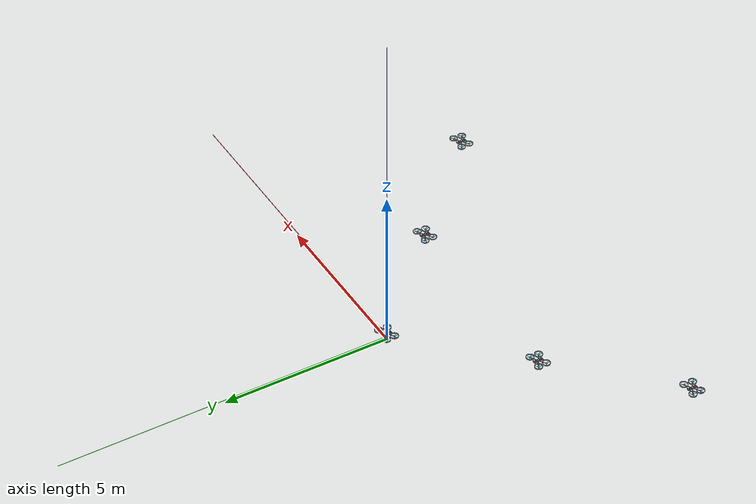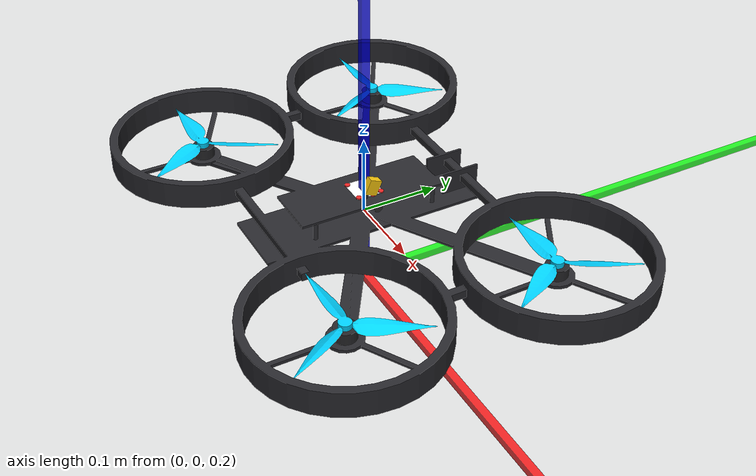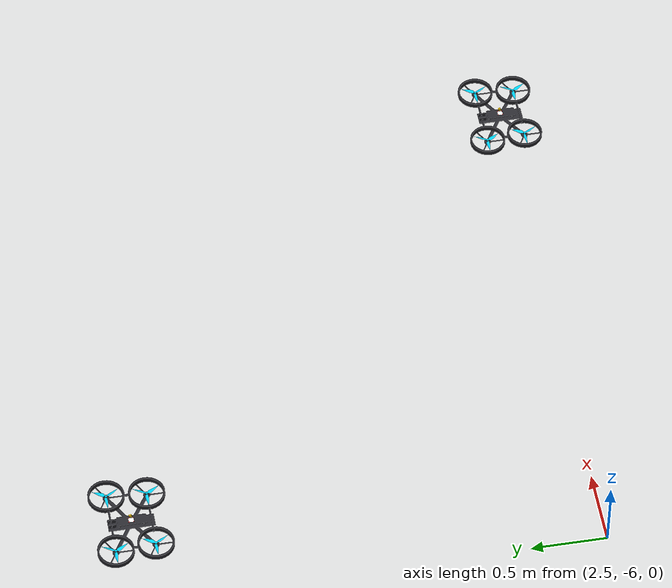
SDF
<sdf version="1.9">
 <world name="cinewhoop_5drones">
  <physics name="1ms" type="ignore">
   <max_step_size>0.001</max_step_size>
   <real_time_factor>1.0</real_time_factor>
  </physics>
  <plugin filename="gz-sim-physics-system" name="gz::sim::systems::Physics"/>
  <plugin filename="gz-sim-sensors-system" name="gz::sim::systems::Sensors">
   <render_engine>ogre2</render_engine>
  </plugin>
  <plugin filename="gz-sim-user-commands-system" name="gz::sim::systems::UserCommands"/>
  <plugin filename="gz-sim-scene-broadcaster-system" name="gz::sim::systems::SceneBroadcaster"/>
  <plugin filename="gz-sim-imu-system" name="gz::sim::systems::Imu"/>
  <plugin filename="gz-sim-navsat-system" name="gz::sim::systems::NavSat"/>
  <scene><ambient>1.0 1.0 1.0</ambient><background>0.8 0.8 0.8</background></scene>
  <spherical_coordinates>
   <latitude_deg>-35.363262</latitude_deg>
   <longitude_deg>149.165237</longitude_deg>
   <elevation>584</elevation>
   <heading_deg>0</heading_deg>
   <surface_model>EARTH_WGS84</surface_model>
  </spherical_coordinates>
  <light type="directional" name="sun">
   <pose>0 0 10 0 0 0</pose>
   <diffuse>0.8 0.8 0.8 1</diffuse>
   <specular>0.8 0.8 0.8 1</specular>
   <attenuation>
    <range>1000</range>
    <constant>0.9</constant>
    <linear>0.01</linear>
    <quadratic>0.001</quadratic>
   </attenuation>
   <direction>-0.5 0.1 -0.9</direction>
  </light>
  <model name="axes">
   <static>1</static>
   <link name="link">
    <visual name="r">
     <cast_shadows>0</cast_shadows>
     <pose>5 0 0.1 0 0 0</pose>
     <geometry><box><size>10 0.01 0.01</size></box></geometry>
     <material>
      <ambient>1 0 0 0.8</ambient>
      <diffuse>1 0 0 0.8</diffuse>
      <emissive>1 0 0 0.8</emissive>
      <specular>0.5 0.5 0.5 0.8</specular>
     </material>
    </visual>
    <visual name="g">
     <cast_shadows>0</cast_shadows>
     <pose>0 5 0.1 0 0 0</pose>
     <geometry><box><size>0.01 10 0.01</size></box></geometry>
     <material>
      <ambient>0 1 0 0.8</ambient>
      <diffuse>0 1 0 0.8</diffuse>
      <emissive>0 1 0 0.8</emissive>
      <specular>0.5 0.5 0.5 0.8</specular>
     </material>
    </visual>
    <visual name="b">
     <cast_shadows>0</cast_shadows>
     <pose>0 0 5.1 0 0 0</pose>
     <geometry><box><size>0.01 0.01 10</size></box></geometry>
     <material>
      <ambient>0 0 1 0.8</ambient>
      <diffuse>0 0 1 0.8</diffuse>
      <emissive>0 0 1 0.8</emissive>
      <specular>0.5 0.5 0.5 0.8</specular>
     </material>
    </visual>
    <sensor name="navsat_sensor" type="navsat"><always_on>1</always_on><update_rate>1</update_rate></sensor>
   </link>
  </model>
  <include>
   <name>cinewhoop_1</name>
   <uri>model://cinewhoop_1</uri>
   <pose degrees="true">0 0 0.2 0 0 90</pose>
  </include>
  <include>
   <name>cinewhoop_2</name>
   <uri>model://cinewhoop_2</uri>
   <pose degrees="true">-3.0 -3.0 0.2 0 0 90</pose>
  </include>
  <include>
   <name>cinewhoop_3</name>
   <uri>model://cinewhoop_3</uri>
   <pose degrees="true">3.0 -3.0 0.2 0 0 90</pose>
  </include>
  <include>
   <name>cinewhoop_4</name>
   <uri>model://cinewhoop_4</uri>
   <pose degrees="true">-6.0 -6.0 0.2 0 0 90</pose>
  </include>
  <include>
   <name>cinewhoop_5</name>
   <uri>model://cinewhoop_5</uri>
   <pose degrees="true">6.0 -6.0 0.2 0 0 90</pose>
  </include>
 </world>
</sdf>

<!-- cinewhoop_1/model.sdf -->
<sdf version="1.9">
  <model name="cinewhoop_1">
    <include>
      <uri>model://iris_with_standoffs</uri>
    </include>

    <!--
      visual markers for debugging
      - blade root    - teal
      - blade tip     - orange
      - blade cp      - yellow
      - blade forward - red
      - blade upward  - blue
    -->

    <!-- plugins -->
    <plugin filename="gz-sim-joint-state-publisher-system"
      name="gz::sim::systems::JointStatePublisher">
    </plugin>
    <plugin filename="gz-sim-lift-drag-system"
        name="gz::sim::systems::LiftDrag">
      <a0>0.3</a0>
      <alpha_stall>1.4</alpha_stall>
      <cla>4.2500</cla>
      <cda>0.10</cda>
      <cma>0.0</cma>
      <cla_stall>-0.025</cla_stall>
      <cda_stall>0.0</cda_stall>
      <cma_stall>0.0</cma_stall>
      <area>0.002</area>
      <air_density>1.2041</air_density>
      <cp>0.084 0 0</cp>
      <forward>0 1 0</forward>
      <upward>0 0 1</upward>
      <link_name>iris_with_standoffs::rotor_0</link_name>
    </plugin>
    <plugin filename="gz-sim-lift-drag-system"
        name="gz::sim::systems::LiftDrag">
      <a0>0.3</a0>
      <alpha_stall>1.4</alpha_stall>
      <cla>4.2500</cla>
      <cda>0.10</cda>
      <cma>0.0</cma>
      <cla_stall>-0.025</cla_stall>
      <cda_stall>0.0</cda_stall>
      <cma_stall>0.0</cma_stall>
      <area>0.002</area>
      <air_density>1.2041</air_density>
      <cp>-0.084 0 0</cp>
      <forward>0 -1 0</forward>
      <upward>0 0 1</upward>
      <link_name>iris_with_standoffs::rotor_0</link_name>
    </plugin>

    <plugin filename="gz-sim-lift-drag-system"
        name="gz::sim::systems::LiftDrag">
      <a0>0.3</a0>
      <alpha_stall>1.4</alpha_stall>
      <cla>4.2500</cla>
      <cda>0.10</cda>
      <cma>0.0</cma>
      <cla_stall>-0.025</cla_stall>
      <cda_stall>0.0</cda_stall>
      <cma_stall>0.0</cma_stall>
      <area>0.002</area>
      <air_density>1.2041</air_density>
      <cp>0.084 0 0</cp>
      <forward>0 1 0</forward>
      <upward>0 0 1</upward>
      <link_name>iris_with_standoffs::rotor_1</link_name>
    </plugin>
    <plugin filename="gz-sim-lift-drag-system"
        name="gz::sim::systems::LiftDrag">
      <a0>0.3</a0>
      <alpha_stall>1.4</alpha_stall>
      <cla>4.2500</cla>
      <cda>0.10</cda>
      <cma>0.0</cma>
      <cla_stall>-0.025</cla_stall>
      <cda_stall>0.0</cda_stall>
      <cma_stall>0.0</cma_stall>
      <area>0.002</area>
      <air_density>1.2041</air_density>
      <cp>-0.084 0 0</cp>
      <forward>0 -1 0</forward>
      <upward>0 0 1</upward>
      <link_name>iris_with_standoffs::rotor_1</link_name>
    </plugin>

    <plugin filename="gz-sim-lift-drag-system"
        name="gz::sim::systems::LiftDrag">
      <a0>0.3</a0>
      <alpha_stall>1.4</alpha_stall>
      <cla>4.2500</cla>
      <cda>0.10</cda>
      <cma>0.0</cma>
      <cla_stall>-0.025</cla_stall>
      <cda_stall>0.0</cda_stall>
      <cma_stall>0.0</cma_stall>
      <area>0.002</area>
      <air_density>1.2041</air_density>
      <cp>0.084 0 0</cp>
      <forward>0 -1 0</forward>
      <upward>0 0 1</upward>
      <link_name>iris_with_standoffs::rotor_2</link_name>
    </plugin>
    <plugin filename="gz-sim-lift-drag-system"
        name="gz::sim::systems::LiftDrag">
      <a0>0.3</a0>
      <alpha_stall>1.4</alpha_stall>
      <cla>4.2500</cla>
      <cda>0.10</cda>
      <cma>0.0</cma>
      <cla_stall>-0.025</cla_stall>
      <cda_stall>0.0</cda_stall>
      <cma_stall>0.0</cma_stall>
      <area>0.002</area>
      <air_density>1.2041</air_density>
      <cp>-0.084 0 0</cp>
      <forward>0 1 0</forward>
      <upward>0 0 1</upward>
      <link_name>iris_with_standoffs::rotor_2</link_name>
    </plugin>

    <plugin filename="gz-sim-lift-drag-system"
        name="gz::sim::systems::LiftDrag">
      <a0>0.3</a0>
      <alpha_stall>1.4</alpha_stall>
      <cla>4.2500</cla>
      <cda>0.10</cda>
      <cma>0.0</cma>
      <cla_stall>-0.025</cla_stall>
      <cda_stall>0.0</cda_stall>
      <cma_stall>0.0</cma_stall>
      <area>0.002</area>
      <air_density>1.2041</air_density>
      <cp>0.084 0 0</cp>
      <forward>0 -1 0</forward>
      <upward>0 0 1</upward>
      <link_name>iris_with_standoffs::rotor_3</link_name>
    </plugin>
    <plugin filename="gz-sim-lift-drag-system"
        name="gz::sim::systems::LiftDrag">
      <a0>0.3</a0>
      <alpha_stall>1.4</alpha_stall>
      <cla>4.2500</cla>
      <cda>0.10</cda>
      <cma>0.0</cma>
      <cla_stall>-0.025</cla_stall>
      <cda_stall>0.0</cda_stall>
      <cma_stall>0.0</cma_stall>
      <area>0.002</area>
      <air_density>1.2041</air_density>
      <cp>-0.084 0 0</cp>
      <forward>0 1 0</forward>
      <upward>0 0 1</upward>
      <link_name>iris_with_standoffs::rotor_3</link_name>
    </plugin>

    <plugin filename="gz-sim-apply-joint-force-system"
      name="gz::sim::systems::ApplyJointForce">
      <joint_name>iris_with_standoffs::rotor_0_joint</joint_name>
    </plugin>
    <plugin filename="gz-sim-apply-joint-force-system"
      name="gz::sim::systems::ApplyJointForce">
      <joint_name>iris_with_standoffs::rotor_1_joint</joint_name>
    </plugin>
    <plugin filename="gz-sim-apply-joint-force-system"
      name="gz::sim::systems::ApplyJointForce">
      <joint_name>iris_with_standoffs::rotor_2_joint</joint_name>
    </plugin>
    <plugin filename="gz-sim-apply-joint-force-system"
      name="gz::sim::systems::ApplyJointForce">
      <joint_name>iris_with_standoffs::rotor_3_joint</joint_name>
    </plugin>

    <plugin name="ArduPilotPlugin"
      filename="ArduPilotPlugin">
      <!-- Port settings -->
      <fdm_addr>127.0.0.1</fdm_addr>
      <fdm_port_in>9002</fdm_port_in>
      <fdm_port_out>9003</fdm_port_out>
      <connectionTimeoutMaxCount>50</connectionTimeoutMaxCount>
      <lock_step>1</lock_step>
      <no_time_sync>1</no_time_sync>
      <have_32_channels>0</have_32_channels>

      <!-- Frame conventions
        Require by ArduPilot: change model and gazebo from XYZ to XY-Z coordinates
      -->
      <modelXYZToAirplaneXForwardZDown degrees="true">0 0 0 180 0 0</modelXYZToAirplaneXForwardZDown>
      <gazeboXYZToNED degrees="true">0 0 0 180 0 90</gazeboXYZToNED>

      <!-- Sensors -->
      <imuName>iris_with_standoffs::imu_link::imu_sensor</imuName>

      <!--
          incoming control command [0, 1]
          so offset it by 0 to get [0, 1]
          and divide max target by 1.
          offset = 0
          multiplier = 838 max rpm / 1 = 838
        -->
      <control channel="0">
        <jointName>iris_with_standoffs::rotor_0_joint</jointName>
        <useForce>1</useForce>
        <multiplier>838</multiplier>
        <offset>0</offset>
        <servo_min>1100</servo_min>
        <servo_max>1900</servo_max>
        <type>VELOCITY</type>
        <p_gain>0.20</p_gain>
        <i_gain>0</i_gain>
        <d_gain>0</d_gain>
        <i_max>0</i_max>
        <i_min>0</i_min>
        <cmd_max>2.5</cmd_max>
        <cmd_min>-2.5</cmd_min>
        <controlVelocitySlowdownSim>1</controlVelocitySlowdownSim>
      </control>

      <control channel="1">
        <jointName>iris_with_standoffs::rotor_1_joint</jointName>
        <useForce>1</useForce>
        <multiplier>838</multiplier>
        <offset>0</offset>
        <servo_min>1100</servo_min>
        <servo_max>1900</servo_max>
        <type>VELOCITY</type>
        <p_gain>0.20</p_gain>
        <i_gain>0</i_gain>
        <d_gain>0</d_gain>
        <i_max>0</i_max>
        <i_min>0</i_min>
        <cmd_max>2.5</cmd_max>
        <cmd_min>-2.5</cmd_min>
        <controlVelocitySlowdownSim>1</controlVelocitySlowdownSim>
      </control>

      <control channel="2">
        <jointName>iris_with_standoffs::rotor_2_joint</jointName>
        <useForce>1</useForce>
        <multiplier>-838</multiplier>
        <offset>0</offset>
        <servo_min>1100</servo_min>
        <servo_max>1900</servo_max>
        <type>VELOCITY</type>
        <p_gain>0.20</p_gain>
        <i_gain>0</i_gain>
        <d_gain>0</d_gain>
        <i_max>0</i_max>
        <i_min>0</i_min>
        <cmd_max>2.5</cmd_max>
        <cmd_min>-2.5</cmd_min>
        <controlVelocitySlowdownSim>1</controlVelocitySlowdownSim>
      </control>

      <control channel="3">
        <jointName>iris_with_standoffs::rotor_3_joint</jointName>
        <useForce>1</useForce>
        <multiplier>-838</multiplier>
        <offset>0</offset>
        <servo_min>1100</servo_min>
        <servo_max>1900</servo_max>
        <type>VELOCITY</type>
        <p_gain>0.20</p_gain>
        <i_gain>0</i_gain>
        <d_gain>0</d_gain>
        <i_max>0</i_max>
        <i_min>0</i_min>
        <cmd_max>2.5</cmd_max>
        <cmd_min>-2.5</cmd_min>
        <controlVelocitySlowdownSim>1</controlVelocitySlowdownSim>
      </control>

    </plugin>

  </model>
</sdf>

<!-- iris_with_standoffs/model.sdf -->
<sdf version='1.9'>
  <model name='iris_with_standoffs'>
    <pose>0 0 0 0 0 0</pose>
    <link name='base_link'>
      <velocity_decay>
        <linear>0.0</linear>
        <angular>0.0</angular>
      </velocity_decay>
      <inertial>
        <pose>0 0 0 0 0 0</pose>
        <mass>1.5</mass>
        <inertia>
          <ixx>0.008</ixx>
          <ixy>0</ixy>
          <ixz>0</ixz>
          <iyy>0.015</iyy>
          <iyz>0</iyz>
          <izz>0.017</izz>
        </inertia>
      </inertial>
      <collision name='base_collision'>
        <pose>0 0 0 0 0 0</pose>
        <geometry>
          <mesh>
            <uri>model://iris_with_standoffs/meshes/iris_collision.stl</uri>
          </mesh>
        </geometry>
        <surface>
          <contact>
            <ode>
              <max_vel>100.0</max_vel>
              <min_depth>0.001</min_depth>
            </ode>
          </contact>
          <friction>
            <ode>
              <mu>100000.0</mu>
              <mu2>100000.0</mu2>
            </ode>
          </friction>
        </surface>
      </collision>
      <collision name='cinewhoop_bottom_collision'>
        <pose>0 0 -0.01 0 0 0</pose>
        <geometry>
          <box>
            <size>0.30 0.30 0.015</size>
          </box>
        </geometry>
        <surface>
          <contact>
            <ode>
              <max_vel>100.0</max_vel>
              <min_depth>0.001</min_depth>
            </ode>
          </contact>
          <friction>
            <ode>
              <mu>100.0</mu>
              <mu2>100.0</mu2>
            </ode>
          </friction>
        </surface>
      </collision>

      <!-- 1. Carbon Fiber Cinewhoop Ducted Frame -->
      <visual name='base_visual'>
        <geometry>
          <mesh>
            <uri>model://iris_with_standoffs/meshes/cinewhoop_frame.dae</uri>
          </mesh>
        </geometry>
        <material>
          <ambient>0.12 0.12 0.14 1.0</ambient>
          <diffuse>0.16 0.16 0.18 1.0</diffuse>
          <specular>0.4 0.4 0.4 1.0</specular>
          <pbr>
            <metal>
              <albedo_map>model://iris_with_standoffs/materials/textures/carbon_fiber_texture.png</albedo_map>
              <metalness>0.2</metalness>
              <roughness>0.5</roughness>
            </metal>
          </pbr>
        </material>
      </visual>

      <!-- 2. Flight Controller Stack: Matek H743-SLIM V3 Top Board -->
      <visual name='matek_h743_fc_visual'>
        <pose>0 0 0.031 0 0 0</pose>
        <geometry>
          <box>
            <size>0.036 0.036 0.003</size>
          </box>
        </geometry>
        <material>
          <diffuse>1.0 1.0 1.0 1.0</diffuse>
          <pbr>
            <metal>
              <albedo_map>model://iris_with_standoffs/materials/textures/matek_pcb_texture.png</albedo_map>
              <roughness>0.25</roughness>
              <metalness>0.20</metalness>
            </metal>
          </pbr>
        </material>
      </visual>

      <!-- 3. Flight Controller Stack: 4-in-1 ESC Bottom Board -->
      <visual name='matek_4in1_esc_visual'>
        <pose>0 0 0.024 0 0 0</pose>
        <geometry>
          <box>
            <size>0.040 0.040 0.003</size>
          </box>
        </geometry>
        <material>
          <ambient>0.08 0.08 0.09 1.0</ambient>
          <diffuse>0.12 0.12 0.13 1.0</diffuse>
          <pbr>
            <metal>
              <roughness>0.7</roughness>
              <metalness>0.1</metalness>
            </metal>
          </pbr>
        </material>
      </visual>

      <!-- 4. Stack Corners: 4 Red Silicone Anti-Vibration Grommets -->
      <visual name='stack_damper_fl'>
        <pose>0.015 0.015 0.0275 0 0 0</pose>
        <geometry>
          <cylinder>
            <radius>0.0035</radius>
            <length>0.012</length>
          </cylinder>
        </geometry>
        <material>
          <ambient>0.80 0.10 0.10 1.0</ambient>
          <diffuse>0.92 0.15 0.15 1.0</diffuse>
          <pbr>
            <metal>
              <roughness>0.6</roughness>
              <metalness>0.05</metalness>
            </metal>
          </pbr>
        </material>
      </visual>
      <visual name='stack_damper_fr'>
        <pose>0.015 -0.015 0.0275 0 0 0</pose>
        <geometry>
          <cylinder>
            <radius>0.0035</radius>
            <length>0.012</length>
          </cylinder>
        </geometry>
        <material>
          <ambient>0.80 0.10 0.10 1.0</ambient>
          <diffuse>0.92 0.15 0.15 1.0</diffuse>
          <pbr>
            <metal>
              <roughness>0.6</roughness>
              <metalness>0.05</metalness>
            </metal>
          </pbr>
        </material>
      </visual>
      <visual name='stack_damper_rl'>
        <pose>-0.015 0.015 0.0275 0 0 0</pose>
        <geometry>
          <cylinder>
            <radius>0.0035</radius>
            <length>0.012</length>
          </cylinder>
        </geometry>
        <material>
          <ambient>0.80 0.10 0.10 1.0</ambient>
          <diffuse>0.92 0.15 0.15 1.0</diffuse>
          <pbr>
            <metal>
              <roughness>0.6</roughness>
              <metalness>0.05</metalness>
            </metal>
          </pbr>
        </material>
      </visual>
      <visual name='stack_damper_rr'>
        <pose>-0.015 -0.015 0.0275 0 0 0</pose>
        <geometry>
          <cylinder>
            <radius>0.0035</radius>
            <length>0.012</length>
          </cylinder>
        </geometry>
        <material>
          <ambient>0.80 0.10 0.10 1.0</ambient>
          <diffuse>0.92 0.15 0.15 1.0</diffuse>
          <pbr>
            <metal>
              <roughness>0.6</roughness>
              <metalness>0.05</metalness>
            </metal>
          </pbr>
        </material>
      </visual>

      <!-- 5. 4 Brushless Motors (Black Anodized Stators & Bells) -->
      <visual name='motor_0_visual'>
        <pose>0.13 -0.22 0.012 0 0 0</pose>
        <geometry>
          <cylinder>
            <radius>0.014</radius>
            <length>0.016</length>
          </cylinder>
        </geometry>
        <material>
          <ambient>0.10 0.10 0.10 1.0</ambient>
          <diffuse>0.15 0.15 0.16 1.0</diffuse>
          <specular>0.6 0.6 0.6 1.0</specular>
          <pbr>
            <metal>
              <roughness>0.35</roughness>
              <metalness>0.85</metalness>
            </metal>
          </pbr>
        </material>
      </visual>
      <visual name='motor_1_visual'>
        <pose>-0.13 0.20 0.012 0 0 0</pose>
        <geometry>
          <cylinder>
            <radius>0.014</radius>
            <length>0.016</length>
          </cylinder>
        </geometry>
        <material>
          <ambient>0.10 0.10 0.10 1.0</ambient>
          <diffuse>0.15 0.15 0.16 1.0</diffuse>
          <specular>0.6 0.6 0.6 1.0</specular>
          <pbr>
            <metal>
              <roughness>0.35</roughness>
              <metalness>0.85</metalness>
            </metal>
          </pbr>
        </material>
      </visual>
      <visual name='motor_2_visual'>
        <pose>0.13 0.22 0.012 0 0 0</pose>
        <geometry>
          <cylinder>
            <radius>0.014</radius>
            <length>0.016</length>
          </cylinder>
        </geometry>
        <material>
          <ambient>0.10 0.10 0.10 1.0</ambient>
          <diffuse>0.15 0.15 0.16 1.0</diffuse>
          <specular>0.6 0.6 0.6 1.0</specular>
          <pbr>
            <metal>
              <roughness>0.35</roughness>
              <metalness>0.85</metalness>
            </metal>
          </pbr>
        </material>
      </visual>
      <visual name='motor_3_visual'>
        <pose>-0.13 -0.20 0.012 0 0 0</pose>
        <geometry>
          <cylinder>
            <radius>0.014</radius>
            <length>0.016</length>
          </cylinder>
        </geometry>
        <material>
          <ambient>0.10 0.10 0.10 1.0</ambient>
          <diffuse>0.15 0.15 0.16 1.0</diffuse>
          <specular>0.6 0.6 0.6 1.0</specular>
          <pbr>
            <metal>
              <roughness>0.35</roughness>
              <metalness>0.85</metalness>
            </metal>
          </pbr>
        </material>
      </visual>

      <!-- 6. Battery Lead Wires & Industrial Yellow XT60 Connector -->
      <visual name='battery_wire_red'>
        <pose>0.005 -0.018 0.038 0 0.40 0</pose>
        <geometry>
          <cylinder>
            <radius>0.0025</radius>
            <length>0.024</length>
          </cylinder>
        </geometry>
        <material>
          <ambient>0.85 0.12 0.12 1.0</ambient>
          <diffuse>0.90 0.15 0.15 1.0</diffuse>
          <pbr>
            <metal>
              <roughness>0.5</roughness>
              <metalness>0.05</metalness>
            </metal>
          </pbr>
        </material>
      </visual>
      <visual name='battery_wire_black'>
        <pose>-0.005 -0.018 0.038 0 0.40 0</pose>
        <geometry>
          <cylinder>
            <radius>0.0025</radius>
            <length>0.024</length>
          </cylinder>
        </geometry>
        <material>
          <ambient>0.08 0.08 0.08 1.0</ambient>
          <diffuse>0.12 0.12 0.12 1.0</diffuse>
          <pbr>
            <metal>
              <roughness>0.5</roughness>
              <metalness>0.05</metalness>
            </metal>
          </pbr>
        </material>
      </visual>
      <visual name='xt60_connector'>
        <pose>0.00 -0.020 0.048 0 0.40 0</pose>
        <geometry>
          <box>
            <size>0.016 0.010 0.020</size>
          </box>
        </geometry>
        <material>
          <ambient>0.92 0.72 0.00 1.0</ambient>
          <diffuse>1.00 0.80 0.05 1.0</diffuse>
          <pbr>
            <metal>
              <roughness>0.3</roughness>
              <metalness>0.1</metalness>
            </metal>
          </pbr>
        </material>
      </visual>

      <!-- 7. Filter Capacitor (Black cylinder with gold band) -->
      <visual name='filter_capacitor'>
        <pose>0.00 -0.028 0.026 1.5708 0 0</pose>
        <geometry>
          <cylinder>
            <radius>0.0055</radius>
            <length>0.018</length>
          </cylinder>
        </geometry>
        <material>
          <ambient>0.10 0.10 0.10 1.0</ambient>
          <diffuse>0.18 0.18 0.18 1.0</diffuse>
          <pbr>
            <metal>
              <roughness>0.3</roughness>
              <metalness>0.7</metalness>
            </metal>
          </pbr>
        </material>
      </visual>

      <!-- 8. Knurled Aluminum Frame Standoffs -->
      <visual name='standoff_fl'>
        <pose>0.08 0.028 0.016 0 0 0</pose>
        <geometry>
          <cylinder>
            <radius>0.003</radius>
            <length>0.026</length>
          </cylinder>
        </geometry>
        <material>
          <ambient>0.12 0.12 0.12 1.0</ambient>
          <diffuse>0.18 0.18 0.20 1.0</diffuse>
          <pbr>
            <metal>
              <roughness>0.3</roughness>
              <metalness>0.8</metalness>
            </metal>
          </pbr>
        </material>
      </visual>
      <visual name='standoff_fr'>
        <pose>0.08 -0.028 0.016 0 0 0</pose>
        <geometry>
          <cylinder>
            <radius>0.003</radius>
            <length>0.026</length>
          </cylinder>
        </geometry>
        <material>
          <ambient>0.12 0.12 0.12 1.0</ambient>
          <diffuse>0.18 0.18 0.20 1.0</diffuse>
          <pbr>
            <metal>
              <roughness>0.3</roughness>
              <metalness>0.8</metalness>
            </metal>
          </pbr>
        </material>
      </visual>
      <visual name='standoff_rl'>
        <pose>-0.08 0.028 0.016 0 0 0</pose>
        <geometry>
          <cylinder>
            <radius>0.003</radius>
            <length>0.026</length>
          </cylinder>
        </geometry>
        <material>
          <ambient>0.12 0.12 0.12 1.0</ambient>
          <diffuse>0.18 0.18 0.20 1.0</diffuse>
          <pbr>
            <metal>
              <roughness>0.3</roughness>
              <metalness>0.8</metalness>
            </metal>
          </pbr>
        </material>
      </visual>
      <visual name='standoff_rr'>
        <pose>-0.08 -0.028 0.016 0 0 0</pose>
        <geometry>
          <cylinder>
            <radius>0.003</radius>
            <length>0.026</length>
          </cylinder>
        </geometry>
        <material>
          <ambient>0.12 0.12 0.12 1.0</ambient>
          <diffuse>0.18 0.18 0.20 1.0</diffuse>
          <pbr>
            <metal>
              <roughness>0.3</roughness>
              <metalness>0.8</metalness>
            </metal>
          </pbr>
        </material>
      </visual>
    </link>

    <link name='imu_link'>
      <inertial>
        <pose>0 0 0 0 0 0</pose>
        <mass>0.15</mass>
        <inertia>
          <ixx>0.00001</ixx>
          <ixy>0</ixy>
          <ixz>0</ixz>
          <iyy>0.00002</iyy>
          <iyz>0</iyz>
          <izz>0.00002</izz>
        </inertia>
      </inertial>
      <sensor name="imu_sensor" type="imu">
        <gz_frame_id>imu_link</gz_frame_id>
        <pose degrees="true">0 0 0 180 0 0</pose>
        <always_on>1</always_on>
        <update_rate>1000.0</update_rate>
      </sensor>
    </link>
    <joint name='imu_joint' type='revolute'>
      <child>imu_link</child>
      <parent>base_link</parent>
      <axis>
        <xyz>0 0 1</xyz>
        <limit>
          <lower>0</lower>
          <upper>0</upper>
          <effort>0</effort>
          <velocity>0</velocity>
        </limit>
        <dynamics>
          <damping>1.0</damping>
        </dynamics>
      </axis>
    </joint>

    <!-- Rotor 0: Front Right, CCW (Gemfan Cyan Tri-Blade) -->
    <link name='rotor_0'>
      <pose>0.13 -0.22 0.023 0 0 0</pose>
      <inertial>
        <pose>0 0 0 0 0 0</pose>
        <mass>0.025</mass>
        <inertia>
          <ixx>9.75e-06</ixx>
          <ixy>0</ixy>
          <ixz>0</ixz>
          <iyy>0.000166704</iyy>
          <iyz>0</iyz>
          <izz>0.000167604</izz>
        </inertia>
      </inertial>
      <collision name='collision'>
        <pose>0 0 0 0 0 0</pose>
        <geometry>
          <cylinder>
            <length>0.005</length>
            <radius>0.1</radius>
          </cylinder>
        </geometry>
      </collision>
      <visual name='visual'>
        <pose>0 0 0 0 0 0</pose>
        <geometry>
          <mesh>
            <scale>1 1 1</scale>
            <uri>model://iris_with_standoffs/meshes/cinewhoop_prop_ccw.dae</uri>
          </mesh>
        </geometry>
        <material>
          <ambient>0.00 0.65 0.95 1.0</ambient>
          <diffuse>0.00 0.82 1.00 1.0</diffuse>
          <specular>0.85 0.85 0.85 1.0</specular>
          <pbr>
            <metal>
              <metalness>0.05</metalness>
              <roughness>0.15</roughness>
            </metal>
          </pbr>
        </material>
      </visual>
    </link>
    <joint name='rotor_0_joint' type='revolute'>
      <child>rotor_0</child>
      <parent>base_link</parent>
      <axis>
        <xyz>0 0 1</xyz>
        <limit>
          <lower>-1e+16</lower>
          <upper>1e+16</upper>
        </limit>
        <dynamics>
          <damping>0.004</damping>
        </dynamics>
      </axis>
    </joint>

    <!-- Rotor 1: Rear Left, CCW (Gemfan Cyan Tri-Blade) -->
    <link name='rotor_1'>
      <pose>-0.13 0.2 0.023 0 0 0</pose>
      <inertial>
        <pose>0 0 0 0 0 0</pose>
        <mass>0.025</mass>
        <inertia>
          <ixx>9.75e-06</ixx>
          <ixy>0</ixy>
          <ixz>0</ixz>
          <iyy>0.000166704</iyy>
          <iyz>0</iyz>
          <izz>0.000167604</izz>
        </inertia>
      </inertial>
      <collision name='collision'>
        <pose>0 0 0 0 0 0</pose>
        <geometry>
          <cylinder>
            <length>0.005</length>
            <radius>0.1</radius>
          </cylinder>
        </geometry>
      </collision>
      <visual name='visual'>
        <pose>0 0 0 0 0 0</pose>
        <geometry>
          <mesh>
            <scale>1 1 1</scale>
            <uri>model://iris_with_standoffs/meshes/cinewhoop_prop_ccw.dae</uri>
          </mesh>
        </geometry>
        <material>
          <ambient>0.00 0.65 0.95 1.0</ambient>
          <diffuse>0.00 0.82 1.00 1.0</diffuse>
          <specular>0.85 0.85 0.85 1.0</specular>
          <pbr>
            <metal>
              <metalness>0.05</metalness>
              <roughness>0.15</roughness>
            </metal>
          </pbr>
        </material>
      </visual>
    </link>
    <joint name='rotor_1_joint' type='revolute'>
      <child>rotor_1</child>
      <parent>base_link</parent>
      <axis>
        <xyz>0 0 1</xyz>
        <limit>
          <lower>-1e+16</lower>
          <upper>1e+16</upper>
        </limit>
        <dynamics>
          <damping>0.004</damping>
        </dynamics>
      </axis>
    </joint>

    <!-- Rotor 2: Front Left, CW (Gemfan Cyan Tri-Blade) -->
    <link name='rotor_2'>
      <pose>0.13 0.22 0.023 0 0 0</pose>
      <inertial>
        <pose>0 0 0 0 0 0</pose>
        <mass>0.025</mass>
        <inertia>
          <ixx>9.75e-06</ixx>
          <ixy>0</ixy>
          <ixz>0</ixz>
          <iyy>0.000166704</iyy>
          <iyz>0</iyz>
          <izz>0.000167604</izz>
        </inertia>
      </inertial>
      <collision name='collision'>
        <pose>0 0 0 0 0 0</pose>
        <geometry>
          <cylinder>
            <length>0.005</length>
            <radius>0.1</radius>
          </cylinder>
        </geometry>
      </collision>
      <visual name='visual'>
        <pose>0 0 0 0 0 0</pose>
        <geometry>
          <mesh>
            <scale>1 1 1</scale>
            <uri>model://iris_with_standoffs/meshes/cinewhoop_prop_cw.dae</uri>
          </mesh>
        </geometry>
        <material>
          <ambient>0.00 0.65 0.95 1.0</ambient>
          <diffuse>0.00 0.82 1.00 1.0</diffuse>
          <specular>0.85 0.85 0.85 1.0</specular>
          <pbr>
            <metal>
              <metalness>0.05</metalness>
              <roughness>0.15</roughness>
            </metal>
          </pbr>
        </material>
      </visual>
    </link>
    <joint name='rotor_2_joint' type='revolute'>
      <child>rotor_2</child>
      <parent>base_link</parent>
      <axis>
        <xyz>0 0 1</xyz>
        <limit>
          <lower>-1e+16</lower>
          <upper>1e+16</upper>
        </limit>
        <dynamics>
          <damping>0.004</damping>
        </dynamics>
      </axis>
    </joint>

    <!-- Rotor 3: Rear Right, CW (Gemfan Cyan Tri-Blade) -->
    <link name='rotor_3'>
      <pose>-0.13 -0.2 0.023 0 0 0</pose>
      <inertial>
        <pose>0 0 0 0 0 0</pose>
        <mass>0.025</mass>
        <inertia>
          <ixx>9.75e-06</ixx>
          <ixy>0</ixy>
          <ixz>0</ixz>
          <iyy>0.000166704</iyy>
          <iyz>0</iyz>
          <izz>0.000167604</izz>
        </inertia>
      </inertial>
      <collision name='collision'>
        <pose>0 0 0 0 0 0</pose>
        <geometry>
          <cylinder>
            <length>0.005</length>
            <radius>0.1</radius>
          </cylinder>
        </geometry>
      </collision>
      <visual name='visual'>
        <pose>0 0 0 0 0 0</pose>
        <geometry>
          <mesh>
            <scale>1 1 1</scale>
            <uri>model://iris_with_standoffs/meshes/cinewhoop_prop_cw.dae</uri>
          </mesh>
        </geometry>
        <material>
          <ambient>0.00 0.65 0.95 1.0</ambient>
          <diffuse>0.00 0.82 1.00 1.0</diffuse>
          <specular>0.85 0.85 0.85 1.0</specular>
          <pbr>
            <metal>
              <metalness>0.05</metalness>
              <roughness>0.15</roughness>
            </metal>
          </pbr>
        </material>
      </visual>
    </link>
    <joint name='rotor_3_joint' type='revolute'>
      <child>rotor_3</child>
      <parent>base_link</parent>
      <axis>
        <xyz>0 0 1</xyz>
        <limit>
          <lower>-1e+16</lower>
          <upper>1e+16</upper>
        </limit>
        <dynamics>
          <damping>0.004</damping>
        </dynamics>
      </axis>
    </joint>
  </model>
</sdf>

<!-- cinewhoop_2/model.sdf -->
<sdf version="1.9">
  <model name="cinewhoop_2">
    <include>
      <uri>model://iris_with_standoffs</uri>
    </include>

    <!--
      visual markers for debugging
      - blade root    - teal
      - blade tip     - orange
      - blade cp      - yellow
      - blade forward - red
      - blade upward  - blue
    -->

    <!-- plugins -->
    <plugin filename="gz-sim-joint-state-publisher-system"
      name="gz::sim::systems::JointStatePublisher">
    </plugin>
    <plugin filename="gz-sim-lift-drag-system"
        name="gz::sim::systems::LiftDrag">
      <a0>0.3</a0>
      <alpha_stall>1.4</alpha_stall>
      <cla>4.2500</cla>
      <cda>0.10</cda>
      <cma>0.0</cma>
      <cla_stall>-0.025</cla_stall>
      <cda_stall>0.0</cda_stall>
      <cma_stall>0.0</cma_stall>
      <area>0.002</area>
      <air_density>1.2041</air_density>
      <cp>0.084 0 0</cp>
      <forward>0 1 0</forward>
      <upward>0 0 1</upward>
      <link_name>iris_with_standoffs::rotor_0</link_name>
    </plugin>
    <plugin filename="gz-sim-lift-drag-system"
        name="gz::sim::systems::LiftDrag">
      <a0>0.3</a0>
      <alpha_stall>1.4</alpha_stall>
      <cla>4.2500</cla>
      <cda>0.10</cda>
      <cma>0.0</cma>
      <cla_stall>-0.025</cla_stall>
      <cda_stall>0.0</cda_stall>
      <cma_stall>0.0</cma_stall>
      <area>0.002</area>
      <air_density>1.2041</air_density>
      <cp>-0.084 0 0</cp>
      <forward>0 -1 0</forward>
      <upward>0 0 1</upward>
      <link_name>iris_with_standoffs::rotor_0</link_name>
    </plugin>

    <plugin filename="gz-sim-lift-drag-system"
        name="gz::sim::systems::LiftDrag">
      <a0>0.3</a0>
      <alpha_stall>1.4</alpha_stall>
      <cla>4.2500</cla>
      <cda>0.10</cda>
      <cma>0.0</cma>
      <cla_stall>-0.025</cla_stall>
      <cda_stall>0.0</cda_stall>
      <cma_stall>0.0</cma_stall>
      <area>0.002</area>
      <air_density>1.2041</air_density>
      <cp>0.084 0 0</cp>
      <forward>0 1 0</forward>
      <upward>0 0 1</upward>
      <link_name>iris_with_standoffs::rotor_1</link_name>
    </plugin>
    <plugin filename="gz-sim-lift-drag-system"
        name="gz::sim::systems::LiftDrag">
      <a0>0.3</a0>
      <alpha_stall>1.4</alpha_stall>
      <cla>4.2500</cla>
      <cda>0.10</cda>
      <cma>0.0</cma>
      <cla_stall>-0.025</cla_stall>
      <cda_stall>0.0</cda_stall>
      <cma_stall>0.0</cma_stall>
      <area>0.002</area>
      <air_density>1.2041</air_density>
      <cp>-0.084 0 0</cp>
      <forward>0 -1 0</forward>
      <upward>0 0 1</upward>
      <link_name>iris_with_standoffs::rotor_1</link_name>
    </plugin>

    <plugin filename="gz-sim-lift-drag-system"
        name="gz::sim::systems::LiftDrag">
      <a0>0.3</a0>
      <alpha_stall>1.4</alpha_stall>
      <cla>4.2500</cla>
      <cda>0.10</cda>
      <cma>0.0</cma>
      <cla_stall>-0.025</cla_stall>
      <cda_stall>0.0</cda_stall>
      <cma_stall>0.0</cma_stall>
      <area>0.002</area>
      <air_density>1.2041</air_density>
      <cp>0.084 0 0</cp>
      <forward>0 -1 0</forward>
      <upward>0 0 1</upward>
      <link_name>iris_with_standoffs::rotor_2</link_name>
    </plugin>
    <plugin filename="gz-sim-lift-drag-system"
        name="gz::sim::systems::LiftDrag">
      <a0>0.3</a0>
      <alpha_stall>1.4</alpha_stall>
      <cla>4.2500</cla>
      <cda>0.10</cda>
      <cma>0.0</cma>
      <cla_stall>-0.025</cla_stall>
      <cda_stall>0.0</cda_stall>
      <cma_stall>0.0</cma_stall>
      <area>0.002</area>
      <air_density>1.2041</air_density>
      <cp>-0.084 0 0</cp>
      <forward>0 1 0</forward>
      <upward>0 0 1</upward>
      <link_name>iris_with_standoffs::rotor_2</link_name>
    </plugin>

    <plugin filename="gz-sim-lift-drag-system"
        name="gz::sim::systems::LiftDrag">
      <a0>0.3</a0>
      <alpha_stall>1.4</alpha_stall>
      <cla>4.2500</cla>
      <cda>0.10</cda>
      <cma>0.0</cma>
      <cla_stall>-0.025</cla_stall>
      <cda_stall>0.0</cda_stall>
      <cma_stall>0.0</cma_stall>
      <area>0.002</area>
      <air_density>1.2041</air_density>
      <cp>0.084 0 0</cp>
      <forward>0 -1 0</forward>
      <upward>0 0 1</upward>
      <link_name>iris_with_standoffs::rotor_3</link_name>
    </plugin>
    <plugin filename="gz-sim-lift-drag-system"
        name="gz::sim::systems::LiftDrag">
      <a0>0.3</a0>
      <alpha_stall>1.4</alpha_stall>
      <cla>4.2500</cla>
      <cda>0.10</cda>
      <cma>0.0</cma>
      <cla_stall>-0.025</cla_stall>
      <cda_stall>0.0</cda_stall>
      <cma_stall>0.0</cma_stall>
      <area>0.002</area>
      <air_density>1.2041</air_density>
      <cp>-0.084 0 0</cp>
      <forward>0 1 0</forward>
      <upward>0 0 1</upward>
      <link_name>iris_with_standoffs::rotor_3</link_name>
    </plugin>

    <plugin filename="gz-sim-apply-joint-force-system"
      name="gz::sim::systems::ApplyJointForce">
      <joint_name>iris_with_standoffs::rotor_0_joint</joint_name>
    </plugin>
    <plugin filename="gz-sim-apply-joint-force-system"
      name="gz::sim::systems::ApplyJointForce">
      <joint_name>iris_with_standoffs::rotor_1_joint</joint_name>
    </plugin>
    <plugin filename="gz-sim-apply-joint-force-system"
      name="gz::sim::systems::ApplyJointForce">
      <joint_name>iris_with_standoffs::rotor_2_joint</joint_name>
    </plugin>
    <plugin filename="gz-sim-apply-joint-force-system"
      name="gz::sim::systems::ApplyJointForce">
      <joint_name>iris_with_standoffs::rotor_3_joint</joint_name>
    </plugin>

    <plugin name="ArduPilotPlugin"
      filename="ArduPilotPlugin">
      <!-- Port settings -->
      <fdm_addr>127.0.0.1</fdm_addr>
      <fdm_port_in>9012</fdm_port_in>
      <fdm_port_out>9013</fdm_port_out>
      <connectionTimeoutMaxCount>50</connectionTimeoutMaxCount>
      <lock_step>1</lock_step>
      <no_time_sync>1</no_time_sync>
      <have_32_channels>0</have_32_channels>

      <!-- Frame conventions
        Require by ArduPilot: change model and gazebo from XYZ to XY-Z coordinates
      -->
      <modelXYZToAirplaneXForwardZDown degrees="true">0 0 0 180 0 0</modelXYZToAirplaneXForwardZDown>
      <gazeboXYZToNED degrees="true">0 0 0 180 0 90</gazeboXYZToNED>

      <!-- Sensors -->
      <imuName>iris_with_standoffs::imu_link::imu_sensor</imuName>

      <!--
          incoming control command [0, 1]
          so offset it by 0 to get [0, 1]
          and divide max target by 1.
          offset = 0
          multiplier = 838 max rpm / 1 = 838
        -->
      <control channel="0">
        <jointName>iris_with_standoffs::rotor_0_joint</jointName>
        <useForce>1</useForce>
        <multiplier>838</multiplier>
        <offset>0</offset>
        <servo_min>1100</servo_min>
        <servo_max>1900</servo_max>
        <type>VELOCITY</type>
        <p_gain>0.20</p_gain>
        <i_gain>0</i_gain>
        <d_gain>0</d_gain>
        <i_max>0</i_max>
        <i_min>0</i_min>
        <cmd_max>2.5</cmd_max>
        <cmd_min>-2.5</cmd_min>
        <controlVelocitySlowdownSim>1</controlVelocitySlowdownSim>
      </control>

      <control channel="1">
        <jointName>iris_with_standoffs::rotor_1_joint</jointName>
        <useForce>1</useForce>
        <multiplier>838</multiplier>
        <offset>0</offset>
        <servo_min>1100</servo_min>
        <servo_max>1900</servo_max>
        <type>VELOCITY</type>
        <p_gain>0.20</p_gain>
        <i_gain>0</i_gain>
        <d_gain>0</d_gain>
        <i_max>0</i_max>
        <i_min>0</i_min>
        <cmd_max>2.5</cmd_max>
        <cmd_min>-2.5</cmd_min>
        <controlVelocitySlowdownSim>1</controlVelocitySlowdownSim>
      </control>

      <control channel="2">
        <jointName>iris_with_standoffs::rotor_2_joint</jointName>
        <useForce>1</useForce>
        <multiplier>-838</multiplier>
        <offset>0</offset>
        <servo_min>1100</servo_min>
        <servo_max>1900</servo_max>
        <type>VELOCITY</type>
        <p_gain>0.20</p_gain>
        <i_gain>0</i_gain>
        <d_gain>0</d_gain>
        <i_max>0</i_max>
        <i_min>0</i_min>
        <cmd_max>2.5</cmd_max>
        <cmd_min>-2.5</cmd_min>
        <controlVelocitySlowdownSim>1</controlVelocitySlowdownSim>
      </control>

      <control channel="3">
        <jointName>iris_with_standoffs::rotor_3_joint</jointName>
        <useForce>1</useForce>
        <multiplier>-838</multiplier>
        <offset>0</offset>
        <servo_min>1100</servo_min>
        <servo_max>1900</servo_max>
        <type>VELOCITY</type>
        <p_gain>0.20</p_gain>
        <i_gain>0</i_gain>
        <d_gain>0</d_gain>
        <i_max>0</i_max>
        <i_min>0</i_min>
        <cmd_max>2.5</cmd_max>
        <cmd_min>-2.5</cmd_min>
        <controlVelocitySlowdownSim>1</controlVelocitySlowdownSim>
      </control>

    </plugin>

  </model>
</sdf>

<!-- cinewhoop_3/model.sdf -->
<sdf version="1.9">
  <model name="cinewhoop_3">
    <include>
      <uri>model://iris_with_standoffs</uri>
    </include>

    <!--
      visual markers for debugging
      - blade root    - teal
      - blade tip     - orange
      - blade cp      - yellow
      - blade forward - red
      - blade upward  - blue
    -->

    <!-- plugins -->
    <plugin filename="gz-sim-joint-state-publisher-system"
      name="gz::sim::systems::JointStatePublisher">
    </plugin>
    <plugin filename="gz-sim-lift-drag-system"
        name="gz::sim::systems::LiftDrag">
      <a0>0.3</a0>
      <alpha_stall>1.4</alpha_stall>
      <cla>4.2500</cla>
      <cda>0.10</cda>
      <cma>0.0</cma>
      <cla_stall>-0.025</cla_stall>
      <cda_stall>0.0</cda_stall>
      <cma_stall>0.0</cma_stall>
      <area>0.002</area>
      <air_density>1.2041</air_density>
      <cp>0.084 0 0</cp>
      <forward>0 1 0</forward>
      <upward>0 0 1</upward>
      <link_name>iris_with_standoffs::rotor_0</link_name>
    </plugin>
    <plugin filename="gz-sim-lift-drag-system"
        name="gz::sim::systems::LiftDrag">
      <a0>0.3</a0>
      <alpha_stall>1.4</alpha_stall>
      <cla>4.2500</cla>
      <cda>0.10</cda>
      <cma>0.0</cma>
      <cla_stall>-0.025</cla_stall>
      <cda_stall>0.0</cda_stall>
      <cma_stall>0.0</cma_stall>
      <area>0.002</area>
      <air_density>1.2041</air_density>
      <cp>-0.084 0 0</cp>
      <forward>0 -1 0</forward>
      <upward>0 0 1</upward>
      <link_name>iris_with_standoffs::rotor_0</link_name>
    </plugin>

    <plugin filename="gz-sim-lift-drag-system"
        name="gz::sim::systems::LiftDrag">
      <a0>0.3</a0>
      <alpha_stall>1.4</alpha_stall>
      <cla>4.2500</cla>
      <cda>0.10</cda>
      <cma>0.0</cma>
      <cla_stall>-0.025</cla_stall>
      <cda_stall>0.0</cda_stall>
      <cma_stall>0.0</cma_stall>
      <area>0.002</area>
      <air_density>1.2041</air_density>
      <cp>0.084 0 0</cp>
      <forward>0 1 0</forward>
      <upward>0 0 1</upward>
      <link_name>iris_with_standoffs::rotor_1</link_name>
    </plugin>
    <plugin filename="gz-sim-lift-drag-system"
        name="gz::sim::systems::LiftDrag">
      <a0>0.3</a0>
      <alpha_stall>1.4</alpha_stall>
      <cla>4.2500</cla>
      <cda>0.10</cda>
      <cma>0.0</cma>
      <cla_stall>-0.025</cla_stall>
      <cda_stall>0.0</cda_stall>
      <cma_stall>0.0</cma_stall>
      <area>0.002</area>
      <air_density>1.2041</air_density>
      <cp>-0.084 0 0</cp>
      <forward>0 -1 0</forward>
      <upward>0 0 1</upward>
      <link_name>iris_with_standoffs::rotor_1</link_name>
    </plugin>

    <plugin filename="gz-sim-lift-drag-system"
        name="gz::sim::systems::LiftDrag">
      <a0>0.3</a0>
      <alpha_stall>1.4</alpha_stall>
      <cla>4.2500</cla>
      <cda>0.10</cda>
      <cma>0.0</cma>
      <cla_stall>-0.025</cla_stall>
      <cda_stall>0.0</cda_stall>
      <cma_stall>0.0</cma_stall>
      <area>0.002</area>
      <air_density>1.2041</air_density>
      <cp>0.084 0 0</cp>
      <forward>0 -1 0</forward>
      <upward>0 0 1</upward>
      <link_name>iris_with_standoffs::rotor_2</link_name>
    </plugin>
    <plugin filename="gz-sim-lift-drag-system"
        name="gz::sim::systems::LiftDrag">
      <a0>0.3</a0>
      <alpha_stall>1.4</alpha_stall>
      <cla>4.2500</cla>
      <cda>0.10</cda>
      <cma>0.0</cma>
      <cla_stall>-0.025</cla_stall>
      <cda_stall>0.0</cda_stall>
      <cma_stall>0.0</cma_stall>
      <area>0.002</area>
      <air_density>1.2041</air_density>
      <cp>-0.084 0 0</cp>
      <forward>0 1 0</forward>
      <upward>0 0 1</upward>
      <link_name>iris_with_standoffs::rotor_2</link_name>
    </plugin>

    <plugin filename="gz-sim-lift-drag-system"
        name="gz::sim::systems::LiftDrag">
      <a0>0.3</a0>
      <alpha_stall>1.4</alpha_stall>
      <cla>4.2500</cla>
      <cda>0.10</cda>
      <cma>0.0</cma>
      <cla_stall>-0.025</cla_stall>
      <cda_stall>0.0</cda_stall>
      <cma_stall>0.0</cma_stall>
      <area>0.002</area>
      <air_density>1.2041</air_density>
      <cp>0.084 0 0</cp>
      <forward>0 -1 0</forward>
      <upward>0 0 1</upward>
      <link_name>iris_with_standoffs::rotor_3</link_name>
    </plugin>
    <plugin filename="gz-sim-lift-drag-system"
        name="gz::sim::systems::LiftDrag">
      <a0>0.3</a0>
      <alpha_stall>1.4</alpha_stall>
      <cla>4.2500</cla>
      <cda>0.10</cda>
      <cma>0.0</cma>
      <cla_stall>-0.025</cla_stall>
      <cda_stall>0.0</cda_stall>
      <cma_stall>0.0</cma_stall>
      <area>0.002</area>
      <air_density>1.2041</air_density>
      <cp>-0.084 0 0</cp>
      <forward>0 1 0</forward>
      <upward>0 0 1</upward>
      <link_name>iris_with_standoffs::rotor_3</link_name>
    </plugin>

    <plugin filename="gz-sim-apply-joint-force-system"
      name="gz::sim::systems::ApplyJointForce">
      <joint_name>iris_with_standoffs::rotor_0_joint</joint_name>
    </plugin>
    <plugin filename="gz-sim-apply-joint-force-system"
      name="gz::sim::systems::ApplyJointForce">
      <joint_name>iris_with_standoffs::rotor_1_joint</joint_name>
    </plugin>
    <plugin filename="gz-sim-apply-joint-force-system"
      name="gz::sim::systems::ApplyJointForce">
      <joint_name>iris_with_standoffs::rotor_2_joint</joint_name>
    </plugin>
    <plugin filename="gz-sim-apply-joint-force-system"
      name="gz::sim::systems::ApplyJointForce">
      <joint_name>iris_with_standoffs::rotor_3_joint</joint_name>
    </plugin>

    <plugin name="ArduPilotPlugin"
      filename="ArduPilotPlugin">
      <!-- Port settings -->
      <fdm_addr>127.0.0.1</fdm_addr>
      <fdm_port_in>9022</fdm_port_in>
      <fdm_port_out>9023</fdm_port_out>
      <connectionTimeoutMaxCount>50</connectionTimeoutMaxCount>
      <lock_step>1</lock_step>
      <no_time_sync>1</no_time_sync>
      <have_32_channels>0</have_32_channels>

      <!-- Frame conventions
        Require by ArduPilot: change model and gazebo from XYZ to XY-Z coordinates
      -->
      <modelXYZToAirplaneXForwardZDown degrees="true">0 0 0 180 0 0</modelXYZToAirplaneXForwardZDown>
      <gazeboXYZToNED degrees="true">0 0 0 180 0 90</gazeboXYZToNED>

      <!-- Sensors -->
      <imuName>iris_with_standoffs::imu_link::imu_sensor</imuName>

      <!--
          incoming control command [0, 1]
          so offset it by 0 to get [0, 1]
          and divide max target by 1.
          offset = 0
          multiplier = 838 max rpm / 1 = 838
        -->
      <control channel="0">
        <jointName>iris_with_standoffs::rotor_0_joint</jointName>
        <useForce>1</useForce>
        <multiplier>838</multiplier>
        <offset>0</offset>
        <servo_min>1100</servo_min>
        <servo_max>1900</servo_max>
        <type>VELOCITY</type>
        <p_gain>0.20</p_gain>
        <i_gain>0</i_gain>
        <d_gain>0</d_gain>
        <i_max>0</i_max>
        <i_min>0</i_min>
        <cmd_max>2.5</cmd_max>
        <cmd_min>-2.5</cmd_min>
        <controlVelocitySlowdownSim>1</controlVelocitySlowdownSim>
      </control>

      <control channel="1">
        <jointName>iris_with_standoffs::rotor_1_joint</jointName>
        <useForce>1</useForce>
        <multiplier>838</multiplier>
        <offset>0</offset>
        <servo_min>1100</servo_min>
        <servo_max>1900</servo_max>
        <type>VELOCITY</type>
        <p_gain>0.20</p_gain>
        <i_gain>0</i_gain>
        <d_gain>0</d_gain>
        <i_max>0</i_max>
        <i_min>0</i_min>
        <cmd_max>2.5</cmd_max>
        <cmd_min>-2.5</cmd_min>
        <controlVelocitySlowdownSim>1</controlVelocitySlowdownSim>
      </control>

      <control channel="2">
        <jointName>iris_with_standoffs::rotor_2_joint</jointName>
        <useForce>1</useForce>
        <multiplier>-838</multiplier>
        <offset>0</offset>
        <servo_min>1100</servo_min>
        <servo_max>1900</servo_max>
        <type>VELOCITY</type>
        <p_gain>0.20</p_gain>
        <i_gain>0</i_gain>
        <d_gain>0</d_gain>
        <i_max>0</i_max>
        <i_min>0</i_min>
        <cmd_max>2.5</cmd_max>
        <cmd_min>-2.5</cmd_min>
        <controlVelocitySlowdownSim>1</controlVelocitySlowdownSim>
      </control>

      <control channel="3">
        <jointName>iris_with_standoffs::rotor_3_joint</jointName>
        <useForce>1</useForce>
        <multiplier>-838</multiplier>
        <offset>0</offset>
        <servo_min>1100</servo_min>
        <servo_max>1900</servo_max>
        <type>VELOCITY</type>
        <p_gain>0.20</p_gain>
        <i_gain>0</i_gain>
        <d_gain>0</d_gain>
        <i_max>0</i_max>
        <i_min>0</i_min>
        <cmd_max>2.5</cmd_max>
        <cmd_min>-2.5</cmd_min>
        <controlVelocitySlowdownSim>1</controlVelocitySlowdownSim>
      </control>

    </plugin>

  </model>
</sdf>

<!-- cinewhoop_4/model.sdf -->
<sdf version="1.9">
  <model name="cinewhoop_4">
    <include>
      <uri>model://iris_with_standoffs</uri>
    </include>

    <!--
      visual markers for debugging
      - blade root    - teal
      - blade tip     - orange
      - blade cp      - yellow
      - blade forward - red
      - blade upward  - blue
    -->

    <!-- plugins -->
    <plugin filename="gz-sim-joint-state-publisher-system"
      name="gz::sim::systems::JointStatePublisher">
    </plugin>
    <plugin filename="gz-sim-lift-drag-system"
        name="gz::sim::systems::LiftDrag">
      <a0>0.3</a0>
      <alpha_stall>1.4</alpha_stall>
      <cla>4.2500</cla>
      <cda>0.10</cda>
      <cma>0.0</cma>
      <cla_stall>-0.025</cla_stall>
      <cda_stall>0.0</cda_stall>
      <cma_stall>0.0</cma_stall>
      <area>0.002</area>
      <air_density>1.2041</air_density>
      <cp>0.084 0 0</cp>
      <forward>0 1 0</forward>
      <upward>0 0 1</upward>
      <link_name>iris_with_standoffs::rotor_0</link_name>
    </plugin>
    <plugin filename="gz-sim-lift-drag-system"
        name="gz::sim::systems::LiftDrag">
      <a0>0.3</a0>
      <alpha_stall>1.4</alpha_stall>
      <cla>4.2500</cla>
      <cda>0.10</cda>
      <cma>0.0</cma>
      <cla_stall>-0.025</cla_stall>
      <cda_stall>0.0</cda_stall>
      <cma_stall>0.0</cma_stall>
      <area>0.002</area>
      <air_density>1.2041</air_density>
      <cp>-0.084 0 0</cp>
      <forward>0 -1 0</forward>
      <upward>0 0 1</upward>
      <link_name>iris_with_standoffs::rotor_0</link_name>
    </plugin>

    <plugin filename="gz-sim-lift-drag-system"
        name="gz::sim::systems::LiftDrag">
      <a0>0.3</a0>
      <alpha_stall>1.4</alpha_stall>
      <cla>4.2500</cla>
      <cda>0.10</cda>
      <cma>0.0</cma>
      <cla_stall>-0.025</cla_stall>
      <cda_stall>0.0</cda_stall>
      <cma_stall>0.0</cma_stall>
      <area>0.002</area>
      <air_density>1.2041</air_density>
      <cp>0.084 0 0</cp>
      <forward>0 1 0</forward>
      <upward>0 0 1</upward>
      <link_name>iris_with_standoffs::rotor_1</link_name>
    </plugin>
    <plugin filename="gz-sim-lift-drag-system"
        name="gz::sim::systems::LiftDrag">
      <a0>0.3</a0>
      <alpha_stall>1.4</alpha_stall>
      <cla>4.2500</cla>
      <cda>0.10</cda>
      <cma>0.0</cma>
      <cla_stall>-0.025</cla_stall>
      <cda_stall>0.0</cda_stall>
      <cma_stall>0.0</cma_stall>
      <area>0.002</area>
      <air_density>1.2041</air_density>
      <cp>-0.084 0 0</cp>
      <forward>0 -1 0</forward>
      <upward>0 0 1</upward>
      <link_name>iris_with_standoffs::rotor_1</link_name>
    </plugin>

    <plugin filename="gz-sim-lift-drag-system"
        name="gz::sim::systems::LiftDrag">
      <a0>0.3</a0>
      <alpha_stall>1.4</alpha_stall>
      <cla>4.2500</cla>
      <cda>0.10</cda>
      <cma>0.0</cma>
      <cla_stall>-0.025</cla_stall>
      <cda_stall>0.0</cda_stall>
      <cma_stall>0.0</cma_stall>
      <area>0.002</area>
      <air_density>1.2041</air_density>
      <cp>0.084 0 0</cp>
      <forward>0 -1 0</forward>
      <upward>0 0 1</upward>
      <link_name>iris_with_standoffs::rotor_2</link_name>
    </plugin>
    <plugin filename="gz-sim-lift-drag-system"
        name="gz::sim::systems::LiftDrag">
      <a0>0.3</a0>
      <alpha_stall>1.4</alpha_stall>
      <cla>4.2500</cla>
      <cda>0.10</cda>
      <cma>0.0</cma>
      <cla_stall>-0.025</cla_stall>
      <cda_stall>0.0</cda_stall>
      <cma_stall>0.0</cma_stall>
      <area>0.002</area>
      <air_density>1.2041</air_density>
      <cp>-0.084 0 0</cp>
      <forward>0 1 0</forward>
      <upward>0 0 1</upward>
      <link_name>iris_with_standoffs::rotor_2</link_name>
    </plugin>

    <plugin filename="gz-sim-lift-drag-system"
        name="gz::sim::systems::LiftDrag">
      <a0>0.3</a0>
      <alpha_stall>1.4</alpha_stall>
      <cla>4.2500</cla>
      <cda>0.10</cda>
      <cma>0.0</cma>
      <cla_stall>-0.025</cla_stall>
      <cda_stall>0.0</cda_stall>
      <cma_stall>0.0</cma_stall>
      <area>0.002</area>
      <air_density>1.2041</air_density>
      <cp>0.084 0 0</cp>
      <forward>0 -1 0</forward>
      <upward>0 0 1</upward>
      <link_name>iris_with_standoffs::rotor_3</link_name>
    </plugin>
    <plugin filename="gz-sim-lift-drag-system"
        name="gz::sim::systems::LiftDrag">
      <a0>0.3</a0>
      <alpha_stall>1.4</alpha_stall>
      <cla>4.2500</cla>
      <cda>0.10</cda>
      <cma>0.0</cma>
      <cla_stall>-0.025</cla_stall>
      <cda_stall>0.0</cda_stall>
      <cma_stall>0.0</cma_stall>
      <area>0.002</area>
      <air_density>1.2041</air_density>
      <cp>-0.084 0 0</cp>
      <forward>0 1 0</forward>
      <upward>0 0 1</upward>
      <link_name>iris_with_standoffs::rotor_3</link_name>
    </plugin>

    <plugin filename="gz-sim-apply-joint-force-system"
      name="gz::sim::systems::ApplyJointForce">
      <joint_name>iris_with_standoffs::rotor_0_joint</joint_name>
    </plugin>
    <plugin filename="gz-sim-apply-joint-force-system"
      name="gz::sim::systems::ApplyJointForce">
      <joint_name>iris_with_standoffs::rotor_1_joint</joint_name>
    </plugin>
    <plugin filename="gz-sim-apply-joint-force-system"
      name="gz::sim::systems::ApplyJointForce">
      <joint_name>iris_with_standoffs::rotor_2_joint</joint_name>
    </plugin>
    <plugin filename="gz-sim-apply-joint-force-system"
      name="gz::sim::systems::ApplyJointForce">
      <joint_name>iris_with_standoffs::rotor_3_joint</joint_name>
    </plugin>

    <plugin name="ArduPilotPlugin"
      filename="ArduPilotPlugin">
      <!-- Port settings -->
      <fdm_addr>127.0.0.1</fdm_addr>
      <fdm_port_in>9032</fdm_port_in>
      <fdm_port_out>9033</fdm_port_out>
      <connectionTimeoutMaxCount>50</connectionTimeoutMaxCount>
      <lock_step>1</lock_step>
      <no_time_sync>1</no_time_sync>
      <have_32_channels>0</have_32_channels>

      <!-- Frame conventions
        Require by ArduPilot: change model and gazebo from XYZ to XY-Z coordinates
      -->
      <modelXYZToAirplaneXForwardZDown degrees="true">0 0 0 180 0 0</modelXYZToAirplaneXForwardZDown>
      <gazeboXYZToNED degrees="true">0 0 0 180 0 90</gazeboXYZToNED>

      <!-- Sensors -->
      <imuName>iris_with_standoffs::imu_link::imu_sensor</imuName>

      <!--
          incoming control command [0, 1]
          so offset it by 0 to get [0, 1]
          and divide max target by 1.
          offset = 0
          multiplier = 838 max rpm / 1 = 838
        -->
      <control channel="0">
        <jointName>iris_with_standoffs::rotor_0_joint</jointName>
        <useForce>1</useForce>
        <multiplier>838</multiplier>
        <offset>0</offset>
        <servo_min>1100</servo_min>
        <servo_max>1900</servo_max>
        <type>VELOCITY</type>
        <p_gain>0.20</p_gain>
        <i_gain>0</i_gain>
        <d_gain>0</d_gain>
        <i_max>0</i_max>
        <i_min>0</i_min>
        <cmd_max>2.5</cmd_max>
        <cmd_min>-2.5</cmd_min>
        <controlVelocitySlowdownSim>1</controlVelocitySlowdownSim>
      </control>

      <control channel="1">
        <jointName>iris_with_standoffs::rotor_1_joint</jointName>
        <useForce>1</useForce>
        <multiplier>838</multiplier>
        <offset>0</offset>
        <servo_min>1100</servo_min>
        <servo_max>1900</servo_max>
        <type>VELOCITY</type>
        <p_gain>0.20</p_gain>
        <i_gain>0</i_gain>
        <d_gain>0</d_gain>
        <i_max>0</i_max>
        <i_min>0</i_min>
        <cmd_max>2.5</cmd_max>
        <cmd_min>-2.5</cmd_min>
        <controlVelocitySlowdownSim>1</controlVelocitySlowdownSim>
      </control>

      <control channel="2">
        <jointName>iris_with_standoffs::rotor_2_joint</jointName>
        <useForce>1</useForce>
        <multiplier>-838</multiplier>
        <offset>0</offset>
        <servo_min>1100</servo_min>
        <servo_max>1900</servo_max>
        <type>VELOCITY</type>
        <p_gain>0.20</p_gain>
        <i_gain>0</i_gain>
        <d_gain>0</d_gain>
        <i_max>0</i_max>
        <i_min>0</i_min>
        <cmd_max>2.5</cmd_max>
        <cmd_min>-2.5</cmd_min>
        <controlVelocitySlowdownSim>1</controlVelocitySlowdownSim>
      </control>

      <control channel="3">
        <jointName>iris_with_standoffs::rotor_3_joint</jointName>
        <useForce>1</useForce>
        <multiplier>-838</multiplier>
        <offset>0</offset>
        <servo_min>1100</servo_min>
        <servo_max>1900</servo_max>
        <type>VELOCITY</type>
        <p_gain>0.20</p_gain>
        <i_gain>0</i_gain>
        <d_gain>0</d_gain>
        <i_max>0</i_max>
        <i_min>0</i_min>
        <cmd_max>2.5</cmd_max>
        <cmd_min>-2.5</cmd_min>
        <controlVelocitySlowdownSim>1</controlVelocitySlowdownSim>
      </control>

    </plugin>

  </model>
</sdf>

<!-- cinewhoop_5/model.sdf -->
<sdf version="1.9">
  <model name="cinewhoop_5">
    <include>
      <uri>model://iris_with_standoffs</uri>
    </include>

    <!--
      visual markers for debugging
      - blade root    - teal
      - blade tip     - orange
      - blade cp      - yellow
      - blade forward - red
      - blade upward  - blue
    -->

    <!-- plugins -->
    <plugin filename="gz-sim-joint-state-publisher-system"
      name="gz::sim::systems::JointStatePublisher">
    </plugin>
    <plugin filename="gz-sim-lift-drag-system"
        name="gz::sim::systems::LiftDrag">
      <a0>0.3</a0>
      <alpha_stall>1.4</alpha_stall>
      <cla>4.2500</cla>
      <cda>0.10</cda>
      <cma>0.0</cma>
      <cla_stall>-0.025</cla_stall>
      <cda_stall>0.0</cda_stall>
      <cma_stall>0.0</cma_stall>
      <area>0.002</area>
      <air_density>1.2041</air_density>
      <cp>0.084 0 0</cp>
      <forward>0 1 0</forward>
      <upward>0 0 1</upward>
      <link_name>iris_with_standoffs::rotor_0</link_name>
    </plugin>
    <plugin filename="gz-sim-lift-drag-system"
        name="gz::sim::systems::LiftDrag">
      <a0>0.3</a0>
      <alpha_stall>1.4</alpha_stall>
      <cla>4.2500</cla>
      <cda>0.10</cda>
      <cma>0.0</cma>
      <cla_stall>-0.025</cla_stall>
      <cda_stall>0.0</cda_stall>
      <cma_stall>0.0</cma_stall>
      <area>0.002</area>
      <air_density>1.2041</air_density>
      <cp>-0.084 0 0</cp>
      <forward>0 -1 0</forward>
      <upward>0 0 1</upward>
      <link_name>iris_with_standoffs::rotor_0</link_name>
    </plugin>

    <plugin filename="gz-sim-lift-drag-system"
        name="gz::sim::systems::LiftDrag">
      <a0>0.3</a0>
      <alpha_stall>1.4</alpha_stall>
      <cla>4.2500</cla>
      <cda>0.10</cda>
      <cma>0.0</cma>
      <cla_stall>-0.025</cla_stall>
      <cda_stall>0.0</cda_stall>
      <cma_stall>0.0</cma_stall>
      <area>0.002</area>
      <air_density>1.2041</air_density>
      <cp>0.084 0 0</cp>
      <forward>0 1 0</forward>
      <upward>0 0 1</upward>
      <link_name>iris_with_standoffs::rotor_1</link_name>
    </plugin>
    <plugin filename="gz-sim-lift-drag-system"
        name="gz::sim::systems::LiftDrag">
      <a0>0.3</a0>
      <alpha_stall>1.4</alpha_stall>
      <cla>4.2500</cla>
      <cda>0.10</cda>
      <cma>0.0</cma>
      <cla_stall>-0.025</cla_stall>
      <cda_stall>0.0</cda_stall>
      <cma_stall>0.0</cma_stall>
      <area>0.002</area>
      <air_density>1.2041</air_density>
      <cp>-0.084 0 0</cp>
      <forward>0 -1 0</forward>
      <upward>0 0 1</upward>
      <link_name>iris_with_standoffs::rotor_1</link_name>
    </plugin>

    <plugin filename="gz-sim-lift-drag-system"
        name="gz::sim::systems::LiftDrag">
      <a0>0.3</a0>
      <alpha_stall>1.4</alpha_stall>
      <cla>4.2500</cla>
      <cda>0.10</cda>
      <cma>0.0</cma>
      <cla_stall>-0.025</cla_stall>
      <cda_stall>0.0</cda_stall>
      <cma_stall>0.0</cma_stall>
      <area>0.002</area>
      <air_density>1.2041</air_density>
      <cp>0.084 0 0</cp>
      <forward>0 -1 0</forward>
      <upward>0 0 1</upward>
      <link_name>iris_with_standoffs::rotor_2</link_name>
    </plugin>
    <plugin filename="gz-sim-lift-drag-system"
        name="gz::sim::systems::LiftDrag">
      <a0>0.3</a0>
      <alpha_stall>1.4</alpha_stall>
      <cla>4.2500</cla>
      <cda>0.10</cda>
      <cma>0.0</cma>
      <cla_stall>-0.025</cla_stall>
      <cda_stall>0.0</cda_stall>
      <cma_stall>0.0</cma_stall>
      <area>0.002</area>
      <air_density>1.2041</air_density>
      <cp>-0.084 0 0</cp>
      <forward>0 1 0</forward>
      <upward>0 0 1</upward>
      <link_name>iris_with_standoffs::rotor_2</link_name>
    </plugin>

    <plugin filename="gz-sim-lift-drag-system"
        name="gz::sim::systems::LiftDrag">
      <a0>0.3</a0>
      <alpha_stall>1.4</alpha_stall>
      <cla>4.2500</cla>
      <cda>0.10</cda>
      <cma>0.0</cma>
      <cla_stall>-0.025</cla_stall>
      <cda_stall>0.0</cda_stall>
      <cma_stall>0.0</cma_stall>
      <area>0.002</area>
      <air_density>1.2041</air_density>
      <cp>0.084 0 0</cp>
      <forward>0 -1 0</forward>
      <upward>0 0 1</upward>
      <link_name>iris_with_standoffs::rotor_3</link_name>
    </plugin>
    <plugin filename="gz-sim-lift-drag-system"
        name="gz::sim::systems::LiftDrag">
      <a0>0.3</a0>
      <alpha_stall>1.4</alpha_stall>
      <cla>4.2500</cla>
      <cda>0.10</cda>
      <cma>0.0</cma>
      <cla_stall>-0.025</cla_stall>
      <cda_stall>0.0</cda_stall>
      <cma_stall>0.0</cma_stall>
      <area>0.002</area>
      <air_density>1.2041</air_density>
      <cp>-0.084 0 0</cp>
      <forward>0 1 0</forward>
      <upward>0 0 1</upward>
      <link_name>iris_with_standoffs::rotor_3</link_name>
    </plugin>

    <plugin filename="gz-sim-apply-joint-force-system"
      name="gz::sim::systems::ApplyJointForce">
      <joint_name>iris_with_standoffs::rotor_0_joint</joint_name>
    </plugin>
    <plugin filename="gz-sim-apply-joint-force-system"
      name="gz::sim::systems::ApplyJointForce">
      <joint_name>iris_with_standoffs::rotor_1_joint</joint_name>
    </plugin>
    <plugin filename="gz-sim-apply-joint-force-system"
      name="gz::sim::systems::ApplyJointForce">
      <joint_name>iris_with_standoffs::rotor_2_joint</joint_name>
    </plugin>
    <plugin filename="gz-sim-apply-joint-force-system"
      name="gz::sim::systems::ApplyJointForce">
      <joint_name>iris_with_standoffs::rotor_3_joint</joint_name>
    </plugin>

    <plugin name="ArduPilotPlugin"
      filename="ArduPilotPlugin">
      <!-- Port settings -->
      <fdm_addr>127.0.0.1</fdm_addr>
      <fdm_port_in>9042</fdm_port_in>
      <fdm_port_out>9043</fdm_port_out>
      <connectionTimeoutMaxCount>50</connectionTimeoutMaxCount>
      <lock_step>1</lock_step>
      <no_time_sync>1</no_time_sync>
      <have_32_channels>0</have_32_channels>

      <!-- Frame conventions
        Require by ArduPilot: change model and gazebo from XYZ to XY-Z coordinates
      -->
      <modelXYZToAirplaneXForwardZDown degrees="true">0 0 0 180 0 0</modelXYZToAirplaneXForwardZDown>
      <gazeboXYZToNED degrees="true">0 0 0 180 0 90</gazeboXYZToNED>

      <!-- Sensors -->
      <imuName>iris_with_standoffs::imu_link::imu_sensor</imuName>

      <!--
          incoming control command [0, 1]
          so offset it by 0 to get [0, 1]
          and divide max target by 1.
          offset = 0
          multiplier = 838 max rpm / 1 = 838
        -->
      <control channel="0">
        <jointName>iris_with_standoffs::rotor_0_joint</jointName>
        <useForce>1</useForce>
        <multiplier>838</multiplier>
        <offset>0</offset>
        <servo_min>1100</servo_min>
        <servo_max>1900</servo_max>
        <type>VELOCITY</type>
        <p_gain>0.20</p_gain>
        <i_gain>0</i_gain>
        <d_gain>0</d_gain>
        <i_max>0</i_max>
        <i_min>0</i_min>
        <cmd_max>2.5</cmd_max>
        <cmd_min>-2.5</cmd_min>
        <controlVelocitySlowdownSim>1</controlVelocitySlowdownSim>
      </control>

      <control channel="1">
        <jointName>iris_with_standoffs::rotor_1_joint</jointName>
        <useForce>1</useForce>
        <multiplier>838</multiplier>
        <offset>0</offset>
        <servo_min>1100</servo_min>
        <servo_max>1900</servo_max>
        <type>VELOCITY</type>
        <p_gain>0.20</p_gain>
        <i_gain>0</i_gain>
        <d_gain>0</d_gain>
        <i_max>0</i_max>
        <i_min>0</i_min>
        <cmd_max>2.5</cmd_max>
        <cmd_min>-2.5</cmd_min>
        <controlVelocitySlowdownSim>1</controlVelocitySlowdownSim>
      </control>

      <control channel="2">
        <jointName>iris_with_standoffs::rotor_2_joint</jointName>
        <useForce>1</useForce>
        <multiplier>-838</multiplier>
        <offset>0</offset>
        <servo_min>1100</servo_min>
        <servo_max>1900</servo_max>
        <type>VELOCITY</type>
        <p_gain>0.20</p_gain>
        <i_gain>0</i_gain>
        <d_gain>0</d_gain>
        <i_max>0</i_max>
        <i_min>0</i_min>
        <cmd_max>2.5</cmd_max>
        <cmd_min>-2.5</cmd_min>
        <controlVelocitySlowdownSim>1</controlVelocitySlowdownSim>
      </control>

      <control channel="3">
        <jointName>iris_with_standoffs::rotor_3_joint</jointName>
        <useForce>1</useForce>
        <multiplier>-838</multiplier>
        <offset>0</offset>
        <servo_min>1100</servo_min>
        <servo_max>1900</servo_max>
        <type>VELOCITY</type>
        <p_gain>0.20</p_gain>
        <i_gain>0</i_gain>
        <d_gain>0</d_gain>
        <i_max>0</i_max>
        <i_min>0</i_min>
        <cmd_max>2.5</cmd_max>
        <cmd_min>-2.5</cmd_min>
        <controlVelocitySlowdownSim>1</controlVelocitySlowdownSim>
      </control>

    </plugin>

  </model>
</sdf>
